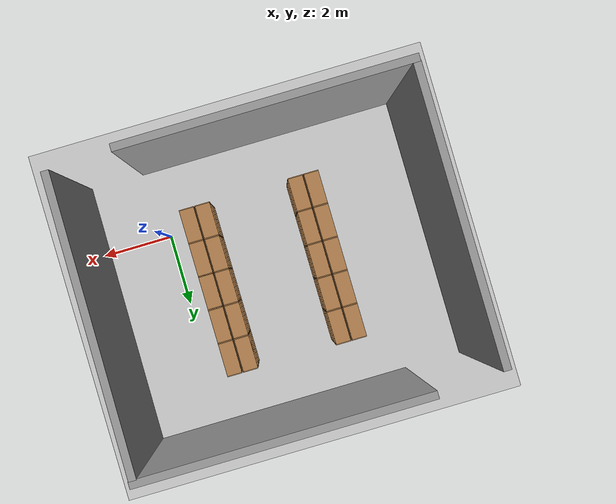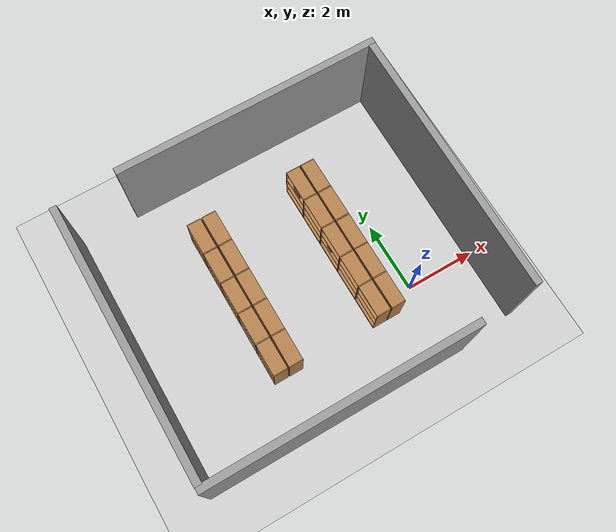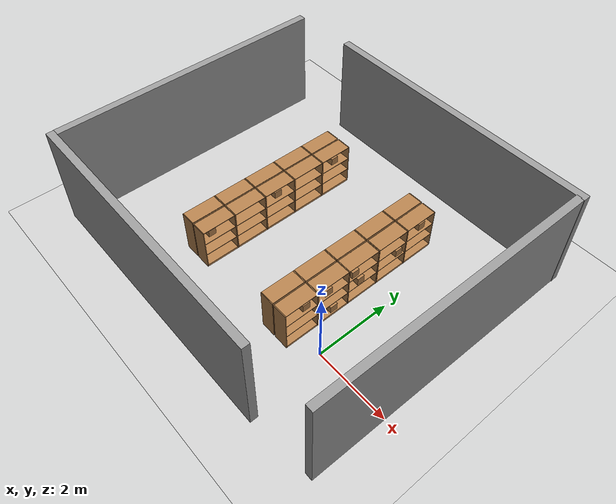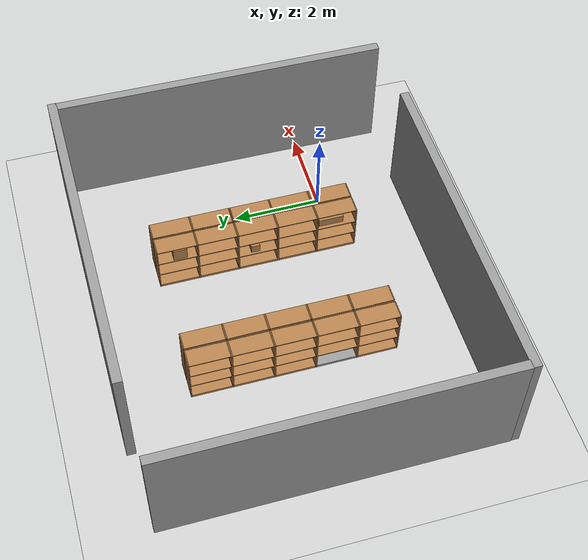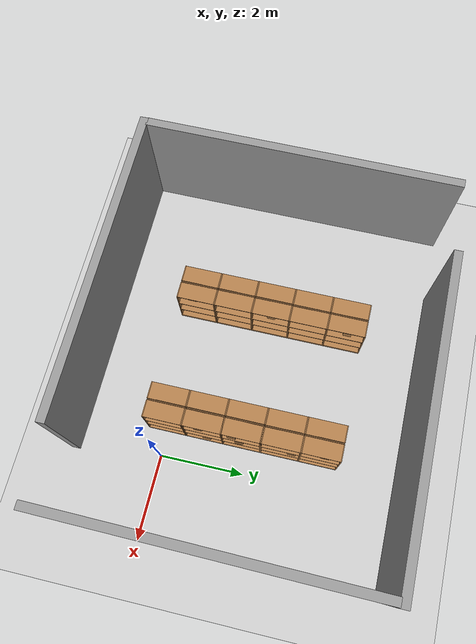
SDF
<sdf version="1.4">
 <world name="default">
  <light name="sun" type="directional">
   <pose>0 0 10 0 -0 0</pose>
   <diffuse>0.8 0.8 0.8 1</diffuse>
   <specular>0.2 0.2 0.2 1</specular>
   <attenuation>
    <range>1000</range>
    <constant>0.9</constant>
    <linear>0.01</linear>
    <quadratic>0.001</quadratic>
   </attenuation>
   <direction>-0.5 0.1 -0.9</direction>
  </light>
  <model name="ground_plane">
   <static>1</static>
   <link name="link">
    <collision name="collision">
     <geometry><plane><normal>0 0 1</normal><size>100 100</size></plane></geometry>
     <surface><friction><ode><mu>100</mu><mu2>50</mu2></ode></friction></surface>
    </collision>
    <visual name="visual">
     <cast_shadows>0</cast_shadows>
     <geometry><plane><normal>0 0 1</normal><size>100 100</size></plane></geometry>
     <material>
      <script><uri>file://media/materials/scripts/gazebo.material</uri><name>Gazebo/Grey</name></script>
     </material>
    </visual>
    <velocity_decay><linear>0</linear><angular>0</angular></velocity_decay>
   </link>
  </model>
  <physics type="ode">
   <max_step_size>0.001</max_step_size>
   <real_time_factor>1</real_time_factor>
   <real_time_update_rate>1000</real_time_update_rate>
   <gravity>0 0 -9.8</gravity>
  </physics>
  <scene><ambient>0.4 0.4 0.4 1</ambient><background>0.7 0.7 0.7 1</background><shadows>1</shadows></scene>
  <spherical_coordinates>
   <surface_model>EARTH_WGS84</surface_model>
   <latitude_deg>0</latitude_deg>
   <longitude_deg>0</longitude_deg>
   <elevation>0</elevation>
   <heading_deg>0</heading_deg>
  </spherical_coordinates>
  <model name="bookshelf">
   <static>0</static>
   <link name="link">
    <inertial><mass>1</mass></inertial>
    <collision name="back">
     <pose>0 0.005 0.6 0 -0 0</pose>
     <geometry><box><size>0.9 0.01 1.2</size></box></geometry>
    </collision>
    <visual name="visual1">
     <pose>0 0.005 0.6 0 -0 0</pose>
     <geometry><box><size>0.9 0.01 1.2</size></box></geometry>
     <material>
      <script><uri>file://media/materials/scripts/gazebo.material</uri><name>Gazebo/Wood</name></script>
     </material>
    </visual>
    <collision name="left_side">
     <pose>0.45 -0.195 0.6 0 -0 0</pose>
     <geometry><box><size>0.02 0.4 1.2</size></box></geometry>
    </collision>
    <visual name="visual2">
     <pose>0.45 -0.195 0.6 0 -0 0</pose>
     <geometry><box><size>0.02 0.4 1.2</size></box></geometry>
     <material>
      <script><uri>file://media/materials/scripts/gazebo.material</uri><name>Gazebo/Wood</name></script>
     </material>
    </visual>
    <collision name="right_side">
     <pose>-0.45 -0.195 0.6 0 -0 0</pose>
     <geometry><box><size>0.02 0.4 1.2</size></box></geometry>
    </collision>
    <visual name="visual3">
     <pose>-0.45 -0.195 0.6 0 -0 0</pose>
     <geometry><box><size>0.02 0.4 1.2</size></box></geometry>
     <material>
      <script><uri>file://media/materials/scripts/gazebo.material</uri><name>Gazebo/Wood</name></script>
     </material>
    </visual>
    <collision name="bottom">
     <pose>0 -0.195 0.03 0 -0 0</pose>
     <geometry><box><size>0.88 0.4 0.06</size></box></geometry>
    </collision>
    <visual name="visual4">
     <pose>0 -0.195 0.03 0 -0 0</pose>
     <geometry><box><size>0.88 0.4 0.06</size></box></geometry>
     <material>
      <script><uri>file://media/materials/scripts/gazebo.material</uri><name>Gazebo/Wood</name></script>
     </material>
    </visual>
    <collision name="top">
     <pose>0 -0.195 1.19 0 -0 0</pose>
     <geometry><box><size>0.88 0.4 0.02</size></box></geometry>
    </collision>
    <visual name="visual5">
     <pose>0 -0.195 1.19 0 -0 0</pose>
     <geometry><box><size>0.88 0.4 0.02</size></box></geometry>
     <material>
      <script><uri>file://media/materials/scripts/gazebo.material</uri><name>Gazebo/Wood</name></script>
     </material>
    </visual>
    <collision name="low_shelf">
     <pose>0 -0.195 0.43 0 -0 0</pose>
     <geometry><box><size>0.88 0.4 0.02</size></box></geometry>
    </collision>
    <visual name="visual6">
     <pose>0 -0.195 0.43 0 -0 0</pose>
     <geometry><box><size>0.88 0.4 0.02</size></box></geometry>
     <material>
      <script><uri>file://media/materials/scripts/gazebo.material</uri><name>Gazebo/Wood</name></script>
     </material>
    </visual>
    <collision name="high_shelf">
     <pose>0 -0.195 0.8 0 -0 0</pose>
     <geometry><box><size>0.88 0.4 0.02</size></box></geometry>
    </collision>
    <visual name="visual7">
     <pose>0 -0.195 0.8 0 -0 0</pose>
     <geometry><box><size>0.88 0.4 0.02</size></box></geometry>
     <material>
      <script><uri>file://media/materials/scripts/gazebo.material</uri><name>Gazebo/Wood</name></script>
     </material>
    </visual>
    <velocity_decay><linear>0</linear><angular>0</angular></velocity_decay>
   </link>
   <pose>-1 0 0 0 -0 1.5708</pose>
  </model>
  <model name="bookshelf_0">
   <static>1</static>
   <link name="link">
    <inertial><mass>1</mass></inertial>
    <collision name="back">
     <pose>0 0.005 0.6 0 -0 0</pose>
     <geometry><box><size>0.9 0.01 1.2</size></box></geometry>
    </collision>
    <visual name="visual1">
     <pose>0 0.005 0.6 0 -0 0</pose>
     <geometry><box><size>0.9 0.01 1.2</size></box></geometry>
     <material>
      <script><uri>file://media/materials/scripts/gazebo.material</uri><name>Gazebo/Wood</name></script>
     </material>
    </visual>
    <collision name="left_side">
     <pose>0.45 -0.195 0.6 0 -0 0</pose>
     <geometry><box><size>0.02 0.4 1.2</size></box></geometry>
    </collision>
    <visual name="visual2">
     <pose>0.45 -0.195 0.6 0 -0 0</pose>
     <geometry><box><size>0.02 0.4 1.2</size></box></geometry>
     <material>
      <script><uri>file://media/materials/scripts/gazebo.material</uri><name>Gazebo/Wood</name></script>
     </material>
    </visual>
    <collision name="right_side">
     <pose>-0.45 -0.195 0.6 0 -0 0</pose>
     <geometry><box><size>0.02 0.4 1.2</size></box></geometry>
    </collision>
    <visual name="visual3">
     <pose>-0.45 -0.195 0.6 0 -0 0</pose>
     <geometry><box><size>0.02 0.4 1.2</size></box></geometry>
     <material>
      <script><uri>file://media/materials/scripts/gazebo.material</uri><name>Gazebo/Wood</name></script>
     </material>
    </visual>
    <collision name="bottom">
     <pose>0 -0.195 0.03 0 -0 0</pose>
     <geometry><box><size>0.88 0.4 0.06</size></box></geometry>
    </collision>
    <visual name="visual4">
     <pose>0 -0.195 0.03 0 -0 0</pose>
     <geometry><box><size>0.88 0.4 0.06</size></box></geometry>
     <material>
      <script><uri>file://media/materials/scripts/gazebo.material</uri><name>Gazebo/Wood</name></script>
     </material>
    </visual>
    <collision name="top">
     <pose>0 -0.195 1.19 0 -0 0</pose>
     <geometry><box><size>0.88 0.4 0.02</size></box></geometry>
    </collision>
    <visual name="visual5">
     <pose>0 -0.195 1.19 0 -0 0</pose>
     <geometry><box><size>0.88 0.4 0.02</size></box></geometry>
     <material>
      <script><uri>file://media/materials/scripts/gazebo.material</uri><name>Gazebo/Wood</name></script>
     </material>
    </visual>
    <collision name="low_shelf">
     <pose>0 -0.195 0.43 0 -0 0</pose>
     <geometry><box><size>0.88 0.4 0.02</size></box></geometry>
    </collision>
    <visual name="visual6">
     <pose>0 -0.195 0.43 0 -0 0</pose>
     <geometry><box><size>0.88 0.4 0.02</size></box></geometry>
     <material>
      <script><uri>file://media/materials/scripts/gazebo.material</uri><name>Gazebo/Wood</name></script>
     </material>
    </visual>
    <collision name="high_shelf">
     <pose>0 -0.195 0.8 0 -0 0</pose>
     <geometry><box><size>0.88 0.4 0.02</size></box></geometry>
    </collision>
    <visual name="visual7">
     <pose>0 -0.195 0.8 0 -0 0</pose>
     <geometry><box><size>0.88 0.4 0.02</size></box></geometry>
     <material>
      <script><uri>file://media/materials/scripts/gazebo.material</uri><name>Gazebo/Wood</name></script>
     </material>
    </visual>
    <velocity_decay><linear>0</linear><angular>0</angular></velocity_decay>
   </link>
   <pose>-1 0.918842 0 0 -0 1.5708</pose>
  </model>
  <model name="bookshelf_1">
   <static>1</static>
   <link name="link">
    <inertial><mass>1</mass></inertial>
    <collision name="back">
     <pose>0 0.005 0.6 0 -0 0</pose>
     <geometry><box><size>0.9 0.01 1.2</size></box></geometry>
    </collision>
    <visual name="visual1">
     <pose>0 0.005 0.6 0 -0 0</pose>
     <geometry><box><size>0.9 0.01 1.2</size></box></geometry>
     <material>
      <script><uri>file://media/materials/scripts/gazebo.material</uri><name>Gazebo/Wood</name></script>
     </material>
    </visual>
    <collision name="left_side">
     <pose>0.45 -0.195 0.6 0 -0 0</pose>
     <geometry><box><size>0.02 0.4 1.2</size></box></geometry>
    </collision>
    <visual name="visual2">
     <pose>0.45 -0.195 0.6 0 -0 0</pose>
     <geometry><box><size>0.02 0.4 1.2</size></box></geometry>
     <material>
      <script><uri>file://media/materials/scripts/gazebo.material</uri><name>Gazebo/Wood</name></script>
     </material>
    </visual>
    <collision name="right_side">
     <pose>-0.45 -0.195 0.6 0 -0 0</pose>
     <geometry><box><size>0.02 0.4 1.2</size></box></geometry>
    </collision>
    <visual name="visual3">
     <pose>-0.45 -0.195 0.6 0 -0 0</pose>
     <geometry><box><size>0.02 0.4 1.2</size></box></geometry>
     <material>
      <script><uri>file://media/materials/scripts/gazebo.material</uri><name>Gazebo/Wood</name></script>
     </material>
    </visual>
    <collision name="bottom">
     <pose>0 -0.195 0.03 0 -0 0</pose>
     <geometry><box><size>0.88 0.4 0.06</size></box></geometry>
    </collision>
    <visual name="visual4">
     <pose>0 -0.195 0.03 0 -0 0</pose>
     <geometry><box><size>0.88 0.4 0.06</size></box></geometry>
     <material>
      <script><uri>file://media/materials/scripts/gazebo.material</uri><name>Gazebo/Wood</name></script>
     </material>
    </visual>
    <collision name="top">
     <pose>0 -0.195 1.19 0 -0 0</pose>
     <geometry><box><size>0.88 0.4 0.02</size></box></geometry>
    </collision>
    <visual name="visual5">
     <pose>0 -0.195 1.19 0 -0 0</pose>
     <geometry><box><size>0.88 0.4 0.02</size></box></geometry>
     <material>
      <script><uri>file://media/materials/scripts/gazebo.material</uri><name>Gazebo/Wood</name></script>
     </material>
    </visual>
    <collision name="low_shelf">
     <pose>0 -0.195 0.43 0 -0 0</pose>
     <geometry><box><size>0.88 0.4 0.02</size></box></geometry>
    </collision>
    <visual name="visual6">
     <pose>0 -0.195 0.43 0 -0 0</pose>
     <geometry><box><size>0.88 0.4 0.02</size></box></geometry>
     <material>
      <script><uri>file://media/materials/scripts/gazebo.material</uri><name>Gazebo/Wood</name></script>
     </material>
    </visual>
    <collision name="high_shelf">
     <pose>0 -0.195 0.8 0 -0 0</pose>
     <geometry><box><size>0.88 0.4 0.02</size></box></geometry>
    </collision>
    <visual name="visual7">
     <pose>0 -0.195 0.8 0 -0 0</pose>
     <geometry><box><size>0.88 0.4 0.02</size></box></geometry>
     <material>
      <script><uri>file://media/materials/scripts/gazebo.material</uri><name>Gazebo/Wood</name></script>
     </material>
    </visual>
    <velocity_decay><linear>0</linear><angular>0</angular></velocity_decay>
   </link>
   <pose>-1 1.83131 0 0 -0 1.5708</pose>
  </model>
  <model name="bookshelf_2">
   <static>1</static>
   <link name="link">
    <inertial><mass>1</mass></inertial>
    <collision name="back">
     <pose>0 0.005 0.6 0 -0 0</pose>
     <geometry><box><size>0.9 0.01 1.2</size></box></geometry>
    </collision>
    <visual name="visual1">
     <pose>0 0.005 0.6 0 -0 0</pose>
     <geometry><box><size>0.9 0.01 1.2</size></box></geometry>
     <material>
      <script><uri>file://media/materials/scripts/gazebo.material</uri><name>Gazebo/Wood</name></script>
     </material>
    </visual>
    <collision name="left_side">
     <pose>0.45 -0.195 0.6 0 -0 0</pose>
     <geometry><box><size>0.02 0.4 1.2</size></box></geometry>
    </collision>
    <visual name="visual2">
     <pose>0.45 -0.195 0.6 0 -0 0</pose>
     <geometry><box><size>0.02 0.4 1.2</size></box></geometry>
     <material>
      <script><uri>file://media/materials/scripts/gazebo.material</uri><name>Gazebo/Wood</name></script>
     </material>
    </visual>
    <collision name="right_side">
     <pose>-0.45 -0.195 0.6 0 -0 0</pose>
     <geometry><box><size>0.02 0.4 1.2</size></box></geometry>
    </collision>
    <visual name="visual3">
     <pose>-0.45 -0.195 0.6 0 -0 0</pose>
     <geometry><box><size>0.02 0.4 1.2</size></box></geometry>
     <material>
      <script><uri>file://media/materials/scripts/gazebo.material</uri><name>Gazebo/Wood</name></script>
     </material>
    </visual>
    <collision name="bottom">
     <pose>0 -0.195 0.03 0 -0 0</pose>
     <geometry><box><size>0.88 0.4 0.06</size></box></geometry>
    </collision>
    <visual name="visual4">
     <pose>0 -0.195 0.03 0 -0 0</pose>
     <geometry><box><size>0.88 0.4 0.06</size></box></geometry>
     <material>
      <script><uri>file://media/materials/scripts/gazebo.material</uri><name>Gazebo/Wood</name></script>
     </material>
    </visual>
    <collision name="top">
     <pose>0 -0.195 1.19 0 -0 0</pose>
     <geometry><box><size>0.88 0.4 0.02</size></box></geometry>
    </collision>
    <visual name="visual5">
     <pose>0 -0.195 1.19 0 -0 0</pose>
     <geometry><box><size>0.88 0.4 0.02</size></box></geometry>
     <material>
      <script><uri>file://media/materials/scripts/gazebo.material</uri><name>Gazebo/Wood</name></script>
     </material>
    </visual>
    <collision name="low_shelf">
     <pose>0 -0.195 0.43 0 -0 0</pose>
     <geometry><box><size>0.88 0.4 0.02</size></box></geometry>
    </collision>
    <visual name="visual6">
     <pose>0 -0.195 0.43 0 -0 0</pose>
     <geometry><box><size>0.88 0.4 0.02</size></box></geometry>
     <material>
      <script><uri>file://media/materials/scripts/gazebo.material</uri><name>Gazebo/Wood</name></script>
     </material>
    </visual>
    <collision name="high_shelf">
     <pose>0 -0.195 0.8 0 -0 0</pose>
     <geometry><box><size>0.88 0.4 0.02</size></box></geometry>
    </collision>
    <visual name="visual7">
     <pose>0 -0.195 0.8 0 -0 0</pose>
     <geometry><box><size>0.88 0.4 0.02</size></box></geometry>
     <material>
      <script><uri>file://media/materials/scripts/gazebo.material</uri><name>Gazebo/Wood</name></script>
     </material>
    </visual>
    <velocity_decay><linear>0</linear><angular>0</angular></velocity_decay>
   </link>
   <pose>-4 1.8376 0 0 -0 1.5708</pose>
  </model>
  <model name="bookshelf_3">
   <static>1</static>
   <link name="link">
    <inertial><mass>1</mass></inertial>
    <collision name="back">
     <pose>0 0.005 0.6 0 -0 0</pose>
     <geometry><box><size>0.9 0.01 1.2</size></box></geometry>
    </collision>
    <visual name="visual1">
     <pose>0 0.005 0.6 0 -0 0</pose>
     <geometry><box><size>0.9 0.01 1.2</size></box></geometry>
     <material>
      <script><uri>file://media/materials/scripts/gazebo.material</uri><name>Gazebo/Wood</name></script>
     </material>
    </visual>
    <collision name="left_side">
     <pose>0.45 -0.195 0.6 0 -0 0</pose>
     <geometry><box><size>0.02 0.4 1.2</size></box></geometry>
    </collision>
    <visual name="visual2">
     <pose>0.45 -0.195 0.6 0 -0 0</pose>
     <geometry><box><size>0.02 0.4 1.2</size></box></geometry>
     <material>
      <script><uri>file://media/materials/scripts/gazebo.material</uri><name>Gazebo/Wood</name></script>
     </material>
    </visual>
    <collision name="right_side">
     <pose>-0.45 -0.195 0.6 0 -0 0</pose>
     <geometry><box><size>0.02 0.4 1.2</size></box></geometry>
    </collision>
    <visual name="visual3">
     <pose>-0.45 -0.195 0.6 0 -0 0</pose>
     <geometry><box><size>0.02 0.4 1.2</size></box></geometry>
     <material>
      <script><uri>file://media/materials/scripts/gazebo.material</uri><name>Gazebo/Wood</name></script>
     </material>
    </visual>
    <collision name="bottom">
     <pose>0 -0.195 0.03 0 -0 0</pose>
     <geometry><box><size>0.88 0.4 0.06</size></box></geometry>
    </collision>
    <visual name="visual4">
     <pose>0 -0.195 0.03 0 -0 0</pose>
     <geometry><box><size>0.88 0.4 0.06</size></box></geometry>
     <material>
      <script><uri>file://media/materials/scripts/gazebo.material</uri><name>Gazebo/Wood</name></script>
     </material>
    </visual>
    <collision name="top">
     <pose>0 -0.195 1.19 0 -0 0</pose>
     <geometry><box><size>0.88 0.4 0.02</size></box></geometry>
    </collision>
    <visual name="visual5">
     <pose>0 -0.195 1.19 0 -0 0</pose>
     <geometry><box><size>0.88 0.4 0.02</size></box></geometry>
     <material>
      <script><uri>file://media/materials/scripts/gazebo.material</uri><name>Gazebo/Wood</name></script>
     </material>
    </visual>
    <collision name="low_shelf">
     <pose>0 -0.195 0.43 0 -0 0</pose>
     <geometry><box><size>0.88 0.4 0.02</size></box></geometry>
    </collision>
    <visual name="visual6">
     <pose>0 -0.195 0.43 0 -0 0</pose>
     <geometry><box><size>0.88 0.4 0.02</size></box></geometry>
     <material>
      <script><uri>file://media/materials/scripts/gazebo.material</uri><name>Gazebo/Wood</name></script>
     </material>
    </visual>
    <collision name="high_shelf">
     <pose>0 -0.195 0.8 0 -0 0</pose>
     <geometry><box><size>0.88 0.4 0.02</size></box></geometry>
    </collision>
    <visual name="visual7">
     <pose>0 -0.195 0.8 0 -0 0</pose>
     <geometry><box><size>0.88 0.4 0.02</size></box></geometry>
     <material>
      <script><uri>file://media/materials/scripts/gazebo.material</uri><name>Gazebo/Wood</name></script>
     </material>
    </visual>
    <velocity_decay><linear>0</linear><angular>0</angular></velocity_decay>
   </link>
   <pose>-4 2.7564 0 0 -0 1.5708</pose>
  </model>
  <model name="bookshelf_4">
   <static>1</static>
   <link name="link">
    <inertial><mass>1</mass></inertial>
    <collision name="back">
     <pose>0 0.005 0.6 0 -0 0</pose>
     <geometry><box><size>0.9 0.01 1.2</size></box></geometry>
    </collision>
    <visual name="visual1">
     <pose>0 0.005 0.6 0 -0 0</pose>
     <geometry><box><size>0.9 0.01 1.2</size></box></geometry>
     <material>
      <script><uri>file://media/materials/scripts/gazebo.material</uri><name>Gazebo/Wood</name></script>
     </material>
    </visual>
    <collision name="left_side">
     <pose>0.45 -0.195 0.6 0 -0 0</pose>
     <geometry><box><size>0.02 0.4 1.2</size></box></geometry>
    </collision>
    <visual name="visual2">
     <pose>0.45 -0.195 0.6 0 -0 0</pose>
     <geometry><box><size>0.02 0.4 1.2</size></box></geometry>
     <material>
      <script><uri>file://media/materials/scripts/gazebo.material</uri><name>Gazebo/Wood</name></script>
     </material>
    </visual>
    <collision name="right_side">
     <pose>-0.45 -0.195 0.6 0 -0 0</pose>
     <geometry><box><size>0.02 0.4 1.2</size></box></geometry>
    </collision>
    <visual name="visual3">
     <pose>-0.45 -0.195 0.6 0 -0 0</pose>
     <geometry><box><size>0.02 0.4 1.2</size></box></geometry>
     <material>
      <script><uri>file://media/materials/scripts/gazebo.material</uri><name>Gazebo/Wood</name></script>
     </material>
    </visual>
    <collision name="bottom">
     <pose>0 -0.195 0.03 0 -0 0</pose>
     <geometry><box><size>0.88 0.4 0.06</size></box></geometry>
    </collision>
    <visual name="visual4">
     <pose>0 -0.195 0.03 0 -0 0</pose>
     <geometry><box><size>0.88 0.4 0.06</size></box></geometry>
     <material>
      <script><uri>file://media/materials/scripts/gazebo.material</uri><name>Gazebo/Wood</name></script>
     </material>
    </visual>
    <collision name="top">
     <pose>0 -0.195 1.19 0 -0 0</pose>
     <geometry><box><size>0.88 0.4 0.02</size></box></geometry>
    </collision>
    <visual name="visual5">
     <pose>0 -0.195 1.19 0 -0 0</pose>
     <geometry><box><size>0.88 0.4 0.02</size></box></geometry>
     <material>
      <script><uri>file://media/materials/scripts/gazebo.material</uri><name>Gazebo/Wood</name></script>
     </material>
    </visual>
    <collision name="low_shelf">
     <pose>0 -0.195 0.43 0 -0 0</pose>
     <geometry><box><size>0.88 0.4 0.02</size></box></geometry>
    </collision>
    <visual name="visual6">
     <pose>0 -0.195 0.43 0 -0 0</pose>
     <geometry><box><size>0.88 0.4 0.02</size></box></geometry>
     <material>
      <script><uri>file://media/materials/scripts/gazebo.material</uri><name>Gazebo/Wood</name></script>
     </material>
    </visual>
    <collision name="high_shelf">
     <pose>0 -0.195 0.8 0 -0 0</pose>
     <geometry><box><size>0.88 0.4 0.02</size></box></geometry>
    </collision>
    <visual name="visual7">
     <pose>0 -0.195 0.8 0 -0 0</pose>
     <geometry><box><size>0.88 0.4 0.02</size></box></geometry>
     <material>
      <script><uri>file://media/materials/scripts/gazebo.material</uri><name>Gazebo/Wood</name></script>
     </material>
    </visual>
    <velocity_decay><linear>0</linear><angular>0</angular></velocity_decay>
   </link>
   <pose>-4 3.6752 0 0 -0 1.5708</pose>
  </model>
  <model name="bookshelf_5">
   <static>1</static>
   <link name="link">
    <inertial><mass>1</mass></inertial>
    <collision name="back">
     <pose>0 0.005 0.6 0 -0 0</pose>
     <geometry><box><size>0.9 0.01 1.2</size></box></geometry>
    </collision>
    <visual name="visual1">
     <pose>0 0.005 0.6 0 -0 0</pose>
     <geometry><box><size>0.9 0.01 1.2</size></box></geometry>
     <material>
      <script><uri>file://media/materials/scripts/gazebo.material</uri><name>Gazebo/Wood</name></script>
     </material>
    </visual>
    <collision name="left_side">
     <pose>0.45 -0.195 0.6 0 -0 0</pose>
     <geometry><box><size>0.02 0.4 1.2</size></box></geometry>
    </collision>
    <visual name="visual2">
     <pose>0.45 -0.195 0.6 0 -0 0</pose>
     <geometry><box><size>0.02 0.4 1.2</size></box></geometry>
     <material>
      <script><uri>file://media/materials/scripts/gazebo.material</uri><name>Gazebo/Wood</name></script>
     </material>
    </visual>
    <collision name="right_side">
     <pose>-0.45 -0.195 0.6 0 -0 0</pose>
     <geometry><box><size>0.02 0.4 1.2</size></box></geometry>
    </collision>
    <visual name="visual3">
     <pose>-0.45 -0.195 0.6 0 -0 0</pose>
     <geometry><box><size>0.02 0.4 1.2</size></box></geometry>
     <material>
      <script><uri>file://media/materials/scripts/gazebo.material</uri><name>Gazebo/Wood</name></script>
     </material>
    </visual>
    <collision name="bottom">
     <pose>0 -0.195 0.03 0 -0 0</pose>
     <geometry><box><size>0.88 0.4 0.06</size></box></geometry>
    </collision>
    <visual name="visual4">
     <pose>0 -0.195 0.03 0 -0 0</pose>
     <geometry><box><size>0.88 0.4 0.06</size></box></geometry>
     <material>
      <script><uri>file://media/materials/scripts/gazebo.material</uri><name>Gazebo/Wood</name></script>
     </material>
    </visual>
    <collision name="top">
     <pose>0 -0.195 1.19 0 -0 0</pose>
     <geometry><box><size>0.88 0.4 0.02</size></box></geometry>
    </collision>
    <visual name="visual5">
     <pose>0 -0.195 1.19 0 -0 0</pose>
     <geometry><box><size>0.88 0.4 0.02</size></box></geometry>
     <material>
      <script><uri>file://media/materials/scripts/gazebo.material</uri><name>Gazebo/Wood</name></script>
     </material>
    </visual>
    <collision name="low_shelf">
     <pose>0 -0.195 0.43 0 -0 0</pose>
     <geometry><box><size>0.88 0.4 0.02</size></box></geometry>
    </collision>
    <visual name="visual6">
     <pose>0 -0.195 0.43 0 -0 0</pose>
     <geometry><box><size>0.88 0.4 0.02</size></box></geometry>
     <material>
      <script><uri>file://media/materials/scripts/gazebo.material</uri><name>Gazebo/Wood</name></script>
     </material>
    </visual>
    <collision name="high_shelf">
     <pose>0 -0.195 0.8 0 -0 0</pose>
     <geometry><box><size>0.88 0.4 0.02</size></box></geometry>
    </collision>
    <visual name="visual7">
     <pose>0 -0.195 0.8 0 -0 0</pose>
     <geometry><box><size>0.88 0.4 0.02</size></box></geometry>
     <material>
      <script><uri>file://media/materials/scripts/gazebo.material</uri><name>Gazebo/Wood</name></script>
     </material>
    </visual>
    <velocity_decay><linear>0</linear><angular>0</angular></velocity_decay>
   </link>
   <pose>-4.05 0 0 0 0 -1.5708</pose>
  </model>
  <model name="bookshelf_6">
   <static>1</static>
   <link name="link">
    <inertial><mass>1</mass></inertial>
    <collision name="back">
     <pose>0 0.005 0.6 0 -0 0</pose>
     <geometry><box><size>0.9 0.01 1.2</size></box></geometry>
    </collision>
    <visual name="visual1">
     <pose>0 0.005 0.6 0 -0 0</pose>
     <geometry><box><size>0.9 0.01 1.2</size></box></geometry>
     <material>
      <script><uri>file://media/materials/scripts/gazebo.material</uri><name>Gazebo/Wood</name></script>
     </material>
    </visual>
    <collision name="left_side">
     <pose>0.45 -0.195 0.6 0 -0 0</pose>
     <geometry><box><size>0.02 0.4 1.2</size></box></geometry>
    </collision>
    <visual name="visual2">
     <pose>0.45 -0.195 0.6 0 -0 0</pose>
     <geometry><box><size>0.02 0.4 1.2</size></box></geometry>
     <material>
      <script><uri>file://media/materials/scripts/gazebo.material</uri><name>Gazebo/Wood</name></script>
     </material>
    </visual>
    <collision name="right_side">
     <pose>-0.45 -0.195 0.6 0 -0 0</pose>
     <geometry><box><size>0.02 0.4 1.2</size></box></geometry>
    </collision>
    <visual name="visual3">
     <pose>-0.45 -0.195 0.6 0 -0 0</pose>
     <geometry><box><size>0.02 0.4 1.2</size></box></geometry>
     <material>
      <script><uri>file://media/materials/scripts/gazebo.material</uri><name>Gazebo/Wood</name></script>
     </material>
    </visual>
    <collision name="bottom">
     <pose>0 -0.195 0.03 0 -0 0</pose>
     <geometry><box><size>0.88 0.4 0.06</size></box></geometry>
    </collision>
    <visual name="visual4">
     <pose>0 -0.195 0.03 0 -0 0</pose>
     <geometry><box><size>0.88 0.4 0.06</size></box></geometry>
     <material>
      <script><uri>file://media/materials/scripts/gazebo.material</uri><name>Gazebo/Grey</name></script>
     </material>
    </visual>
    <collision name="top">
     <pose>0 -0.195 1.19 0 -0 0</pose>
     <geometry><box><size>0.88 0.4 0.02</size></box></geometry>
    </collision>
    <visual name="visual5">
     <pose>0 -0.195 1.19 0 -0 0</pose>
     <geometry><box><size>0.88 0.4 0.02</size></box></geometry>
     <material>
      <script><uri>file://media/materials/scripts/gazebo.material</uri><name>Gazebo/Wood</name></script>
     </material>
    </visual>
    <collision name="low_shelf">
     <pose>0 -0.195 0.43 0 -0 0</pose>
     <geometry><box><size>0.88 0.4 0.02</size></box></geometry>
    </collision>
    <visual name="visual6">
     <pose>0 -0.195 0.43 0 -0 0</pose>
     <geometry><box><size>0.88 0.4 0.02</size></box></geometry>
     <material>
      <script><uri>file://media/materials/scripts/gazebo.material</uri><name>Gazebo/Wood</name></script>
     </material>
    </visual>
    <collision name="high_shelf">
     <pose>0 -0.195 0.8 0 -0 0</pose>
     <geometry><box><size>0.88 0.4 0.02</size></box></geometry>
    </collision>
    <visual name="visual7">
     <pose>0 -0.195 0.8 0 -0 0</pose>
     <geometry><box><size>0.88 0.4 0.02</size></box></geometry>
     <material>
      <script><uri>file://media/materials/scripts/gazebo.material</uri><name>Gazebo/Wood</name></script>
     </material>
    </visual>
    <velocity_decay><linear>0</linear><angular>0</angular></velocity_decay>
   </link>
   <pose>-4.05 0.9188 0 0 0 -1.5708</pose>
  </model>
  <model name="bookshelf_7">
   <static>1</static>
   <link name="link">
    <inertial><mass>1</mass></inertial>
    <collision name="back">
     <pose>0 0.005 0.6 0 -0 0</pose>
     <geometry><box><size>0.9 0.01 1.2</size></box></geometry>
    </collision>
    <visual name="visual1">
     <pose>0 0.005 0.6 0 -0 0</pose>
     <geometry><box><size>0.9 0.01 1.2</size></box></geometry>
     <material>
      <script><uri>file://media/materials/scripts/gazebo.material</uri><name>Gazebo/Wood</name></script>
     </material>
    </visual>
    <collision name="left_side">
     <pose>0.45 -0.195 0.6 0 -0 0</pose>
     <geometry><box><size>0.02 0.4 1.2</size></box></geometry>
    </collision>
    <visual name="visual2">
     <pose>0.45 -0.195 0.6 0 -0 0</pose>
     <geometry><box><size>0.02 0.4 1.2</size></box></geometry>
     <material>
      <script><uri>file://media/materials/scripts/gazebo.material</uri><name>Gazebo/Wood</name></script>
     </material>
    </visual>
    <collision name="right_side">
     <pose>-0.45 -0.195 0.6 0 -0 0</pose>
     <geometry><box><size>0.02 0.4 1.2</size></box></geometry>
    </collision>
    <visual name="visual3">
     <pose>-0.45 -0.195 0.6 0 -0 0</pose>
     <geometry><box><size>0.02 0.4 1.2</size></box></geometry>
     <material>
      <script><uri>file://media/materials/scripts/gazebo.material</uri><name>Gazebo/Wood</name></script>
     </material>
    </visual>
    <collision name="bottom">
     <pose>0 -0.195 0.03 0 -0 0</pose>
     <geometry><box><size>0.88 0.4 0.06</size></box></geometry>
    </collision>
    <visual name="visual4">
     <pose>0 -0.195 0.03 0 -0 0</pose>
     <geometry><box><size>0.88 0.4 0.06</size></box></geometry>
     <material>
      <script><uri>file://media/materials/scripts/gazebo.material</uri><name>Gazebo/Wood</name></script>
     </material>
    </visual>
    <collision name="top">
     <pose>0 -0.195 1.19 0 -0 0</pose>
     <geometry><box><size>0.88 0.4 0.02</size></box></geometry>
    </collision>
    <visual name="visual5">
     <pose>0 -0.195 1.19 0 -0 0</pose>
     <geometry><box><size>0.88 0.4 0.02</size></box></geometry>
     <material>
      <script><uri>file://media/materials/scripts/gazebo.material</uri><name>Gazebo/Wood</name></script>
     </material>
    </visual>
    <collision name="low_shelf">
     <pose>0 -0.195 0.43 0 -0 0</pose>
     <geometry><box><size>0.88 0.4 0.02</size></box></geometry>
    </collision>
    <visual name="visual6">
     <pose>0 -0.195 0.43 0 -0 0</pose>
     <geometry><box><size>0.88 0.4 0.02</size></box></geometry>
     <material>
      <script><uri>file://media/materials/scripts/gazebo.material</uri><name>Gazebo/Wood</name></script>
     </material>
    </visual>
    <collision name="high_shelf">
     <pose>0 -0.195 0.8 0 -0 0</pose>
     <geometry><box><size>0.88 0.4 0.02</size></box></geometry>
    </collision>
    <visual name="visual7">
     <pose>0 -0.195 0.8 0 -0 0</pose>
     <geometry><box><size>0.88 0.4 0.02</size></box></geometry>
     <material>
      <script><uri>file://media/materials/scripts/gazebo.material</uri><name>Gazebo/Wood</name></script>
     </material>
    </visual>
    <velocity_decay><linear>0</linear><angular>0</angular></velocity_decay>
   </link>
   <pose>-4.05 1.8376 0 0 0 -1.5708</pose>
  </model>
  <model name="bookshelf_8">
   <static>1</static>
   <link name="link">
    <inertial><mass>1</mass></inertial>
    <collision name="back">
     <pose>0 0.005 0.6 0 -0 0</pose>
     <geometry><box><size>0.9 0.01 1.2</size></box></geometry>
    </collision>
    <visual name="visual1">
     <pose>0 0.005 0.6 0 -0 0</pose>
     <geometry><box><size>0.9 0.01 1.2</size></box></geometry>
     <material>
      <script><uri>file://media/materials/scripts/gazebo.material</uri><name>Gazebo/Wood</name></script>
     </material>
    </visual>
    <collision name="left_side">
     <pose>0.45 -0.195 0.6 0 -0 0</pose>
     <geometry><box><size>0.02 0.4 1.2</size></box></geometry>
    </collision>
    <visual name="visual2">
     <pose>0.45 -0.195 0.6 0 -0 0</pose>
     <geometry><box><size>0.02 0.4 1.2</size></box></geometry>
     <material>
      <script><uri>file://media/materials/scripts/gazebo.material</uri><name>Gazebo/Wood</name></script>
     </material>
    </visual>
    <collision name="right_side">
     <pose>-0.45 -0.195 0.6 0 -0 0</pose>
     <geometry><box><size>0.02 0.4 1.2</size></box></geometry>
    </collision>
    <visual name="visual3">
     <pose>-0.45 -0.195 0.6 0 -0 0</pose>
     <geometry><box><size>0.02 0.4 1.2</size></box></geometry>
     <material>
      <script><uri>file://media/materials/scripts/gazebo.material</uri><name>Gazebo/Wood</name></script>
     </material>
    </visual>
    <collision name="bottom">
     <pose>0 -0.195 0.03 0 -0 0</pose>
     <geometry><box><size>0.88 0.4 0.06</size></box></geometry>
    </collision>
    <visual name="visual4">
     <pose>0 -0.195 0.03 0 -0 0</pose>
     <geometry><box><size>0.88 0.4 0.06</size></box></geometry>
     <material>
      <script><uri>file://media/materials/scripts/gazebo.material</uri><name>Gazebo/Wood</name></script>
     </material>
    </visual>
    <collision name="top">
     <pose>0 -0.195 1.19 0 -0 0</pose>
     <geometry><box><size>0.88 0.4 0.02</size></box></geometry>
    </collision>
    <visual name="visual5">
     <pose>0 -0.195 1.19 0 -0 0</pose>
     <geometry><box><size>0.88 0.4 0.02</size></box></geometry>
     <material>
      <script><uri>file://media/materials/scripts/gazebo.material</uri><name>Gazebo/Wood</name></script>
     </material>
    </visual>
    <collision name="low_shelf">
     <pose>0 -0.195 0.43 0 -0 0</pose>
     <geometry><box><size>0.88 0.4 0.02</size></box></geometry>
    </collision>
    <visual name="visual6">
     <pose>0 -0.195 0.43 0 -0 0</pose>
     <geometry><box><size>0.88 0.4 0.02</size></box></geometry>
     <material>
      <script><uri>file://media/materials/scripts/gazebo.material</uri><name>Gazebo/Wood</name></script>
     </material>
    </visual>
    <collision name="high_shelf">
     <pose>0 -0.195 0.8 0 -0 0</pose>
     <geometry><box><size>0.88 0.4 0.02</size></box></geometry>
    </collision>
    <visual name="visual7">
     <pose>0 -0.195 0.8 0 -0 0</pose>
     <geometry><box><size>0.88 0.4 0.02</size></box></geometry>
     <material>
      <script><uri>file://media/materials/scripts/gazebo.material</uri><name>Gazebo/Wood</name></script>
     </material>
    </visual>
    <velocity_decay><linear>0</linear><angular>0</angular></velocity_decay>
   </link>
   <pose>-4.05 2.7564 0 0 0 -1.5708</pose>
  </model>
  <model name="bookshelf_9">
   <static>1</static>
   <link name="link">
    <inertial><mass>1</mass></inertial>
    <collision name="back">
     <pose>0 0.005 0.6 0 -0 0</pose>
     <geometry><box><size>0.9 0.01 1.2</size></box></geometry>
    </collision>
    <visual name="visual1">
     <pose>0 0.005 0.6 0 -0 0</pose>
     <geometry><box><size>0.9 0.01 1.2</size></box></geometry>
     <material>
      <script><uri>file://media/materials/scripts/gazebo.material</uri><name>Gazebo/Wood</name></script>
     </material>
    </visual>
    <collision name="left_side">
     <pose>0.45 -0.195 0.6 0 -0 0</pose>
     <geometry><box><size>0.02 0.4 1.2</size></box></geometry>
    </collision>
    <visual name="visual2">
     <pose>0.45 -0.195 0.6 0 -0 0</pose>
     <geometry><box><size>0.02 0.4 1.2</size></box></geometry>
     <material>
      <script><uri>file://media/materials/scripts/gazebo.material</uri><name>Gazebo/Wood</name></script>
     </material>
    </visual>
    <collision name="right_side">
     <pose>-0.45 -0.195 0.6 0 -0 0</pose>
     <geometry><box><size>0.02 0.4 1.2</size></box></geometry>
    </collision>
    <visual name="visual3">
     <pose>-0.45 -0.195 0.6 0 -0 0</pose>
     <geometry><box><size>0.02 0.4 1.2</size></box></geometry>
     <material>
      <script><uri>file://media/materials/scripts/gazebo.material</uri><name>Gazebo/Wood</name></script>
     </material>
    </visual>
    <collision name="bottom">
     <pose>0 -0.195 0.03 0 -0 0</pose>
     <geometry><box><size>0.88 0.4 0.06</size></box></geometry>
    </collision>
    <visual name="visual4">
     <pose>0 -0.195 0.03 0 -0 0</pose>
     <geometry><box><size>0.88 0.4 0.06</size></box></geometry>
     <material>
      <script><uri>file://media/materials/scripts/gazebo.material</uri><name>Gazebo/Wood</name></script>
     </material>
    </visual>
    <collision name="top">
     <pose>0 -0.195 1.19 0 -0 0</pose>
     <geometry><box><size>0.88 0.4 0.02</size></box></geometry>
    </collision>
    <visual name="visual5">
     <pose>0 -0.195 1.19 0 -0 0</pose>
     <geometry><box><size>0.88 0.4 0.02</size></box></geometry>
     <material>
      <script><uri>file://media/materials/scripts/gazebo.material</uri><name>Gazebo/Wood</name></script>
     </material>
    </visual>
    <collision name="low_shelf">
     <pose>0 -0.195 0.43 0 -0 0</pose>
     <geometry><box><size>0.88 0.4 0.02</size></box></geometry>
    </collision>
    <visual name="visual6">
     <pose>0 -0.195 0.43 0 -0 0</pose>
     <geometry><box><size>0.88 0.4 0.02</size></box></geometry>
     <material>
      <script><uri>file://media/materials/scripts/gazebo.material</uri><name>Gazebo/Wood</name></script>
     </material>
    </visual>
    <collision name="high_shelf">
     <pose>0 -0.195 0.8 0 -0 0</pose>
     <geometry><box><size>0.88 0.4 0.02</size></box></geometry>
    </collision>
    <visual name="visual7">
     <pose>0 -0.195 0.8 0 -0 0</pose>
     <geometry><box><size>0.88 0.4 0.02</size></box></geometry>
     <material>
      <script><uri>file://media/materials/scripts/gazebo.material</uri><name>Gazebo/Wood</name></script>
     </material>
    </visual>
    <velocity_decay><linear>0</linear><angular>0</angular></velocity_decay>
   </link>
   <pose>-4.05 3.6752 0 0 0 -1.5708</pose>
  </model>
  <model name="bookshelf_10">
   <static>1</static>
   <link name="link">
    <inertial><mass>1</mass></inertial>
    <collision name="back">
     <pose>0 0.005 0.6 0 -0 0</pose>
     <geometry><box><size>0.9 0.01 1.2</size></box></geometry>
    </collision>
    <visual name="visual1">
     <pose>0 0.005 0.6 0 -0 0</pose>
     <geometry><box><size>0.9 0.01 1.2</size></box></geometry>
     <material>
      <script><uri>file://media/materials/scripts/gazebo.material</uri><name>Gazebo/Wood</name></script>
     </material>
    </visual>
    <collision name="left_side">
     <pose>0.45 -0.195 0.6 0 -0 0</pose>
     <geometry><box><size>0.02 0.4 1.2</size></box></geometry>
    </collision>
    <visual name="visual2">
     <pose>0.45 -0.195 0.6 0 -0 0</pose>
     <geometry><box><size>0.02 0.4 1.2</size></box></geometry>
     <material>
      <script><uri>file://media/materials/scripts/gazebo.material</uri><name>Gazebo/Wood</name></script>
     </material>
    </visual>
    <collision name="right_side">
     <pose>-0.45 -0.195 0.6 0 -0 0</pose>
     <geometry><box><size>0.02 0.4 1.2</size></box></geometry>
    </collision>
    <visual name="visual3">
     <pose>-0.45 -0.195 0.6 0 -0 0</pose>
     <geometry><box><size>0.02 0.4 1.2</size></box></geometry>
     <material>
      <script><uri>file://media/materials/scripts/gazebo.material</uri><name>Gazebo/Wood</name></script>
     </material>
    </visual>
    <collision name="bottom">
     <pose>0 -0.195 0.03 0 -0 0</pose>
     <geometry><box><size>0.88 0.4 0.06</size></box></geometry>
    </collision>
    <visual name="visual4">
     <pose>0 -0.195 0.03 0 -0 0</pose>
     <geometry><box><size>0.88 0.4 0.06</size></box></geometry>
     <material>
      <script><uri>file://media/materials/scripts/gazebo.material</uri><name>Gazebo/Wood</name></script>
     </material>
    </visual>
    <collision name="top">
     <pose>0 -0.195 1.19 0 -0 0</pose>
     <geometry><box><size>0.88 0.4 0.02</size></box></geometry>
    </collision>
    <visual name="visual5">
     <pose>0 -0.195 1.19 0 -0 0</pose>
     <geometry><box><size>0.88 0.4 0.02</size></box></geometry>
     <material>
      <script><uri>file://media/materials/scripts/gazebo.material</uri><name>Gazebo/Wood</name></script>
     </material>
    </visual>
    <collision name="low_shelf">
     <pose>0 -0.195 0.43 0 -0 0</pose>
     <geometry><box><size>0.88 0.4 0.02</size></box></geometry>
    </collision>
    <visual name="visual6">
     <pose>0 -0.195 0.43 0 -0 0</pose>
     <geometry><box><size>0.88 0.4 0.02</size></box></geometry>
     <material>
      <script><uri>file://media/materials/scripts/gazebo.material</uri><name>Gazebo/Wood</name></script>
     </material>
    </visual>
    <collision name="high_shelf">
     <pose>0 -0.195 0.8 0 -0 0</pose>
     <geometry><box><size>0.88 0.4 0.02</size></box></geometry>
    </collision>
    <visual name="visual7">
     <pose>0 -0.195 0.8 0 -0 0</pose>
     <geometry><box><size>0.88 0.4 0.02</size></box></geometry>
     <material>
      <script><uri>file://media/materials/scripts/gazebo.material</uri><name>Gazebo/Wood</name></script>
     </material>
    </visual>
    <velocity_decay><linear>0</linear><angular>0</angular></velocity_decay>
   </link>
   <pose>-1 2.7564 0 0 -0 1.5708</pose>
  </model>
  <model name="bookshelf_11">
   <static>1</static>
   <link name="link">
    <inertial><mass>1</mass></inertial>
    <collision name="back">
     <pose>0 0.005 0.6 0 -0 0</pose>
     <geometry><box><size>0.9 0.01 1.2</size></box></geometry>
    </collision>
    <visual name="visual1">
     <pose>0 0.005 0.6 0 -0 0</pose>
     <geometry><box><size>0.9 0.01 1.2</size></box></geometry>
     <material>
      <script><uri>file://media/materials/scripts/gazebo.material</uri><name>Gazebo/Wood</name></script>
     </material>
    </visual>
    <collision name="left_side">
     <pose>0.45 -0.195 0.6 0 -0 0</pose>
     <geometry><box><size>0.02 0.4 1.2</size></box></geometry>
    </collision>
    <visual name="visual2">
     <pose>0.45 -0.195 0.6 0 -0 0</pose>
     <geometry><box><size>0.02 0.4 1.2</size></box></geometry>
     <material>
      <script><uri>file://media/materials/scripts/gazebo.material</uri><name>Gazebo/Wood</name></script>
     </material>
    </visual>
    <collision name="right_side">
     <pose>-0.45 -0.195 0.6 0 -0 0</pose>
     <geometry><box><size>0.02 0.4 1.2</size></box></geometry>
    </collision>
    <visual name="visual3">
     <pose>-0.45 -0.195 0.6 0 -0 0</pose>
     <geometry><box><size>0.02 0.4 1.2</size></box></geometry>
     <material>
      <script><uri>file://media/materials/scripts/gazebo.material</uri><name>Gazebo/Wood</name></script>
     </material>
    </visual>
    <collision name="bottom">
     <pose>0 -0.195 0.03 0 -0 0</pose>
     <geometry><box><size>0.88 0.4 0.06</size></box></geometry>
    </collision>
    <visual name="visual4">
     <pose>0 -0.195 0.03 0 -0 0</pose>
     <geometry><box><size>0.88 0.4 0.06</size></box></geometry>
     <material>
      <script><uri>file://media/materials/scripts/gazebo.material</uri><name>Gazebo/Wood</name></script>
     </material>
    </visual>
    <collision name="top">
     <pose>0 -0.195 1.19 0 -0 0</pose>
     <geometry><box><size>0.88 0.4 0.02</size></box></geometry>
    </collision>
    <visual name="visual5">
     <pose>0 -0.195 1.19 0 -0 0</pose>
     <geometry><box><size>0.88 0.4 0.02</size></box></geometry>
     <material>
      <script><uri>file://media/materials/scripts/gazebo.material</uri><name>Gazebo/Wood</name></script>
     </material>
    </visual>
    <collision name="low_shelf">
     <pose>0 -0.195 0.43 0 -0 0</pose>
     <geometry><box><size>0.88 0.4 0.02</size></box></geometry>
    </collision>
    <visual name="visual6">
     <pose>0 -0.195 0.43 0 -0 0</pose>
     <geometry><box><size>0.88 0.4 0.02</size></box></geometry>
     <material>
      <script><uri>file://media/materials/scripts/gazebo.material</uri><name>Gazebo/Wood</name></script>
     </material>
    </visual>
    <collision name="high_shelf">
     <pose>0 -0.195 0.8 0 -0 0</pose>
     <geometry><box><size>0.88 0.4 0.02</size></box></geometry>
    </collision>
    <visual name="visual7">
     <pose>0 -0.195 0.8 0 -0 0</pose>
     <geometry><box><size>0.88 0.4 0.02</size></box></geometry>
     <material>
      <script><uri>file://media/materials/scripts/gazebo.material</uri><name>Gazebo/Wood</name></script>
     </material>
    </visual>
    <velocity_decay><linear>0</linear><angular>0</angular></velocity_decay>
   </link>
   <pose>-1 3.6752 0 0 -0 1.5708</pose>
  </model>
  <model name="bookshelf_12">
   <static>1</static>
   <link name="link">
    <inertial><mass>1</mass></inertial>
    <collision name="back">
     <pose>0 0.005 0.6 0 -0 0</pose>
     <geometry><box><size>0.9 0.01 1.2</size></box></geometry>
    </collision>
    <visual name="visual1">
     <pose>0 0.005 0.6 0 -0 0</pose>
     <geometry><box><size>0.9 0.01 1.2</size></box></geometry>
     <material>
      <script><uri>file://media/materials/scripts/gazebo.material</uri><name>Gazebo/Wood</name></script>
     </material>
    </visual>
    <collision name="left_side">
     <pose>0.45 -0.195 0.6 0 -0 0</pose>
     <geometry><box><size>0.02 0.4 1.2</size></box></geometry>
    </collision>
    <visual name="visual2">
     <pose>0.45 -0.195 0.6 0 -0 0</pose>
     <geometry><box><size>0.02 0.4 1.2</size></box></geometry>
     <material>
      <script><uri>file://media/materials/scripts/gazebo.material</uri><name>Gazebo/Wood</name></script>
     </material>
    </visual>
    <collision name="right_side">
     <pose>-0.45 -0.195 0.6 0 -0 0</pose>
     <geometry><box><size>0.02 0.4 1.2</size></box></geometry>
    </collision>
    <visual name="visual3">
     <pose>-0.45 -0.195 0.6 0 -0 0</pose>
     <geometry><box><size>0.02 0.4 1.2</size></box></geometry>
     <material>
      <script><uri>file://media/materials/scripts/gazebo.material</uri><name>Gazebo/Wood</name></script>
     </material>
    </visual>
    <collision name="bottom">
     <pose>0 -0.195 0.03 0 -0 0</pose>
     <geometry><box><size>0.88 0.4 0.06</size></box></geometry>
    </collision>
    <visual name="visual4">
     <pose>0 -0.195 0.03 0 -0 0</pose>
     <geometry><box><size>0.88 0.4 0.06</size></box></geometry>
     <material>
      <script><uri>file://media/materials/scripts/gazebo.material</uri><name>Gazebo/Wood</name></script>
     </material>
    </visual>
    <collision name="top">
     <pose>0 -0.195 1.19 0 -0 0</pose>
     <geometry><box><size>0.88 0.4 0.02</size></box></geometry>
    </collision>
    <visual name="visual5">
     <pose>0 -0.195 1.19 0 -0 0</pose>
     <geometry><box><size>0.88 0.4 0.02</size></box></geometry>
     <material>
      <script><uri>file://media/materials/scripts/gazebo.material</uri><name>Gazebo/Wood</name></script>
     </material>
    </visual>
    <collision name="low_shelf">
     <pose>0 -0.195 0.43 0 -0 0</pose>
     <geometry><box><size>0.88 0.4 0.02</size></box></geometry>
    </collision>
    <visual name="visual6">
     <pose>0 -0.195 0.43 0 -0 0</pose>
     <geometry><box><size>0.88 0.4 0.02</size></box></geometry>
     <material>
      <script><uri>file://media/materials/scripts/gazebo.material</uri><name>Gazebo/Wood</name></script>
     </material>
    </visual>
    <collision name="high_shelf">
     <pose>0 -0.195 0.8 0 -0 0</pose>
     <geometry><box><size>0.88 0.4 0.02</size></box></geometry>
    </collision>
    <visual name="visual7">
     <pose>0 -0.195 0.8 0 -0 0</pose>
     <geometry><box><size>0.88 0.4 0.02</size></box></geometry>
     <material>
      <script><uri>file://media/materials/scripts/gazebo.material</uri><name>Gazebo/Wood</name></script>
     </material>
    </visual>
    <velocity_decay><linear>0</linear><angular>0</angular></velocity_decay>
   </link>
   <pose>-1.04916 0 0 0 0 -1.5708</pose>
  </model>
  <model name="bookshelf_13">
   <static>1</static>
   <link name="link">
    <inertial><mass>1</mass></inertial>
    <collision name="back">
     <pose>0 0.005 0.6 0 -0 0</pose>
     <geometry><box><size>0.9 0.01 1.2</size></box></geometry>
    </collision>
    <visual name="visual1">
     <pose>0 0.005 0.6 0 -0 0</pose>
     <geometry><box><size>0.9 0.01 1.2</size></box></geometry>
     <material>
      <script><uri>file://media/materials/scripts/gazebo.material</uri><name>Gazebo/Wood</name></script>
     </material>
    </visual>
    <collision name="left_side">
     <pose>0.45 -0.195 0.6 0 -0 0</pose>
     <geometry><box><size>0.02 0.4 1.2</size></box></geometry>
    </collision>
    <visual name="visual2">
     <pose>0.45 -0.195 0.6 0 -0 0</pose>
     <geometry><box><size>0.02 0.4 1.2</size></box></geometry>
     <material>
      <script><uri>file://media/materials/scripts/gazebo.material</uri><name>Gazebo/Wood</name></script>
     </material>
    </visual>
    <collision name="right_side">
     <pose>-0.45 -0.195 0.6 0 -0 0</pose>
     <geometry><box><size>0.02 0.4 1.2</size></box></geometry>
    </collision>
    <visual name="visual3">
     <pose>-0.45 -0.195 0.6 0 -0 0</pose>
     <geometry><box><size>0.02 0.4 1.2</size></box></geometry>
     <material>
      <script><uri>file://media/materials/scripts/gazebo.material</uri><name>Gazebo/Wood</name></script>
     </material>
    </visual>
    <collision name="bottom">
     <pose>0 -0.195 0.03 0 -0 0</pose>
     <geometry><box><size>0.88 0.4 0.06</size></box></geometry>
    </collision>
    <visual name="visual4">
     <pose>0 -0.195 0.03 0 -0 0</pose>
     <geometry><box><size>0.88 0.4 0.06</size></box></geometry>
     <material>
      <script><uri>file://media/materials/scripts/gazebo.material</uri><name>Gazebo/Wood</name></script>
     </material>
    </visual>
    <collision name="top">
     <pose>0 -0.195 1.19 0 -0 0</pose>
     <geometry><box><size>0.88 0.4 0.02</size></box></geometry>
    </collision>
    <visual name="visual5">
     <pose>0 -0.195 1.19 0 -0 0</pose>
     <geometry><box><size>0.88 0.4 0.02</size></box></geometry>
     <material>
      <script><uri>file://media/materials/scripts/gazebo.material</uri><name>Gazebo/Wood</name></script>
     </material>
    </visual>
    <collision name="low_shelf">
     <pose>0 -0.195 0.43 0 -0 0</pose>
     <geometry><box><size>0.88 0.4 0.02</size></box></geometry>
    </collision>
    <visual name="visual6">
     <pose>0 -0.195 0.43 0 -0 0</pose>
     <geometry><box><size>0.88 0.4 0.02</size></box></geometry>
     <material>
      <script><uri>file://media/materials/scripts/gazebo.material</uri><name>Gazebo/Wood</name></script>
     </material>
    </visual>
    <collision name="high_shelf">
     <pose>0 -0.195 0.8 0 -0 0</pose>
     <geometry><box><size>0.88 0.4 0.02</size></box></geometry>
    </collision>
    <visual name="visual7">
     <pose>0 -0.195 0.8 0 -0 0</pose>
     <geometry><box><size>0.88 0.4 0.02</size></box></geometry>
     <material>
      <script><uri>file://media/materials/scripts/gazebo.material</uri><name>Gazebo/Wood</name></script>
     </material>
    </visual>
    <velocity_decay><linear>0</linear><angular>0</angular></velocity_decay>
   </link>
   <pose>-1.04916 0.9188 0 0 0 -1.5708</pose>
  </model>
  <model name="bookshelf_14">
   <static>1</static>
   <link name="link">
    <inertial><mass>1</mass></inertial>
    <collision name="back">
     <pose>0 0.005 0.6 0 -0 0</pose>
     <geometry><box><size>0.9 0.01 1.2</size></box></geometry>
    </collision>
    <visual name="visual1">
     <pose>0 0.005 0.6 0 -0 0</pose>
     <geometry><box><size>0.9 0.01 1.2</size></box></geometry>
     <material>
      <script><uri>file://media/materials/scripts/gazebo.material</uri><name>Gazebo/Wood</name></script>
     </material>
    </visual>
    <collision name="left_side">
     <pose>0.45 -0.195 0.6 0 -0 0</pose>
     <geometry><box><size>0.02 0.4 1.2</size></box></geometry>
    </collision>
    <visual name="visual2">
     <pose>0.45 -0.195 0.6 0 -0 0</pose>
     <geometry><box><size>0.02 0.4 1.2</size></box></geometry>
     <material>
      <script><uri>file://media/materials/scripts/gazebo.material</uri><name>Gazebo/Wood</name></script>
     </material>
    </visual>
    <collision name="right_side">
     <pose>-0.45 -0.195 0.6 0 -0 0</pose>
     <geometry><box><size>0.02 0.4 1.2</size></box></geometry>
    </collision>
    <visual name="visual3">
     <pose>-0.45 -0.195 0.6 0 -0 0</pose>
     <geometry><box><size>0.02 0.4 1.2</size></box></geometry>
     <material>
      <script><uri>file://media/materials/scripts/gazebo.material</uri><name>Gazebo/Wood</name></script>
     </material>
    </visual>
    <collision name="bottom">
     <pose>0 -0.195 0.03 0 -0 0</pose>
     <geometry><box><size>0.88 0.4 0.06</size></box></geometry>
    </collision>
    <visual name="visual4">
     <pose>0 -0.195 0.03 0 -0 0</pose>
     <geometry><box><size>0.88 0.4 0.06</size></box></geometry>
     <material>
      <script><uri>file://media/materials/scripts/gazebo.material</uri><name>Gazebo/Wood</name></script>
     </material>
    </visual>
    <collision name="top">
     <pose>0 -0.195 1.19 0 -0 0</pose>
     <geometry><box><size>0.88 0.4 0.02</size></box></geometry>
    </collision>
    <visual name="visual5">
     <pose>0 -0.195 1.19 0 -0 0</pose>
     <geometry><box><size>0.88 0.4 0.02</size></box></geometry>
     <material>
      <script><uri>file://media/materials/scripts/gazebo.material</uri><name>Gazebo/Wood</name></script>
     </material>
    </visual>
    <collision name="low_shelf">
     <pose>0 -0.195 0.43 0 -0 0</pose>
     <geometry><box><size>0.88 0.4 0.02</size></box></geometry>
    </collision>
    <visual name="visual6">
     <pose>0 -0.195 0.43 0 -0 0</pose>
     <geometry><box><size>0.88 0.4 0.02</size></box></geometry>
     <material>
      <script><uri>file://media/materials/scripts/gazebo.material</uri><name>Gazebo/Wood</name></script>
     </material>
    </visual>
    <collision name="high_shelf">
     <pose>0 -0.195 0.8 0 -0 0</pose>
     <geometry><box><size>0.88 0.4 0.02</size></box></geometry>
    </collision>
    <visual name="visual7">
     <pose>0 -0.195 0.8 0 -0 0</pose>
     <geometry><box><size>0.88 0.4 0.02</size></box></geometry>
     <material>
      <script><uri>file://media/materials/scripts/gazebo.material</uri><name>Gazebo/Wood</name></script>
     </material>
    </visual>
    <velocity_decay><linear>0</linear><angular>0</angular></velocity_decay>
   </link>
   <pose>-1.04916 1.8376 0 0 0 -1.5708</pose>
  </model>
  <model name="bookshelf_15">
   <static>1</static>
   <link name="link">
    <inertial><mass>1</mass></inertial>
    <collision name="back">
     <pose>0 0.005 0.6 0 -0 0</pose>
     <geometry><box><size>0.9 0.01 1.2</size></box></geometry>
    </collision>
    <visual name="visual1">
     <pose>0 0.005 0.6 0 -0 0</pose>
     <geometry><box><size>0.9 0.01 1.2</size></box></geometry>
     <material>
      <script><uri>file://media/materials/scripts/gazebo.material</uri><name>Gazebo/Wood</name></script>
     </material>
    </visual>
    <collision name="left_side">
     <pose>0.45 -0.195 0.6 0 -0 0</pose>
     <geometry><box><size>0.02 0.4 1.2</size></box></geometry>
    </collision>
    <visual name="visual2">
     <pose>0.45 -0.195 0.6 0 -0 0</pose>
     <geometry><box><size>0.02 0.4 1.2</size></box></geometry>
     <material>
      <script><uri>file://media/materials/scripts/gazebo.material</uri><name>Gazebo/Wood</name></script>
     </material>
    </visual>
    <collision name="right_side">
     <pose>-0.45 -0.195 0.6 0 -0 0</pose>
     <geometry><box><size>0.02 0.4 1.2</size></box></geometry>
    </collision>
    <visual name="visual3">
     <pose>-0.45 -0.195 0.6 0 -0 0</pose>
     <geometry><box><size>0.02 0.4 1.2</size></box></geometry>
     <material>
      <script><uri>file://media/materials/scripts/gazebo.material</uri><name>Gazebo/Wood</name></script>
     </material>
    </visual>
    <collision name="bottom">
     <pose>0 -0.195 0.03 0 -0 0</pose>
     <geometry><box><size>0.88 0.4 0.06</size></box></geometry>
    </collision>
    <visual name="visual4">
     <pose>0 -0.195 0.03 0 -0 0</pose>
     <geometry><box><size>0.88 0.4 0.06</size></box></geometry>
     <material>
      <script><uri>file://media/materials/scripts/gazebo.material</uri><name>Gazebo/Wood</name></script>
     </material>
    </visual>
    <collision name="top">
     <pose>0 -0.195 1.19 0 -0 0</pose>
     <geometry><box><size>0.88 0.4 0.02</size></box></geometry>
    </collision>
    <visual name="visual5">
     <pose>0 -0.195 1.19 0 -0 0</pose>
     <geometry><box><size>0.88 0.4 0.02</size></box></geometry>
     <material>
      <script><uri>file://media/materials/scripts/gazebo.material</uri><name>Gazebo/Wood</name></script>
     </material>
    </visual>
    <collision name="low_shelf">
     <pose>0 -0.195 0.43 0 -0 0</pose>
     <geometry><box><size>0.88 0.4 0.02</size></box></geometry>
    </collision>
    <visual name="visual6">
     <pose>0 -0.195 0.43 0 -0 0</pose>
     <geometry><box><size>0.88 0.4 0.02</size></box></geometry>
     <material>
      <script><uri>file://media/materials/scripts/gazebo.material</uri><name>Gazebo/Wood</name></script>
     </material>
    </visual>
    <collision name="high_shelf">
     <pose>0 -0.195 0.8 0 -0 0</pose>
     <geometry><box><size>0.88 0.4 0.02</size></box></geometry>
    </collision>
    <visual name="visual7">
     <pose>0 -0.195 0.8 0 -0 0</pose>
     <geometry><box><size>0.88 0.4 0.02</size></box></geometry>
     <material>
      <script><uri>file://media/materials/scripts/gazebo.material</uri><name>Gazebo/Wood</name></script>
     </material>
    </visual>
    <velocity_decay><linear>0</linear><angular>0</angular></velocity_decay>
   </link>
   <pose>-1.04916 2.7564 0 0 0 -1.5708</pose>
  </model>
  <model name="bookshelf_16">
   <static>1</static>
   <link name="link">
    <inertial><mass>1</mass></inertial>
    <collision name="back">
     <pose>0 0.005 0.6 0 -0 0</pose>
     <geometry><box><size>0.9 0.01 1.2</size></box></geometry>
    </collision>
    <visual name="visual1">
     <pose>0 0.005 0.6 0 -0 0</pose>
     <geometry><box><size>0.9 0.01 1.2</size></box></geometry>
     <material>
      <script><uri>file://media/materials/scripts/gazebo.material</uri><name>Gazebo/Wood</name></script>
     </material>
    </visual>
    <collision name="left_side">
     <pose>0.45 -0.195 0.6 0 -0 0</pose>
     <geometry><box><size>0.02 0.4 1.2</size></box></geometry>
    </collision>
    <visual name="visual2">
     <pose>0.45 -0.195 0.6 0 -0 0</pose>
     <geometry><box><size>0.02 0.4 1.2</size></box></geometry>
     <material>
      <script><uri>file://media/materials/scripts/gazebo.material</uri><name>Gazebo/Wood</name></script>
     </material>
    </visual>
    <collision name="right_side">
     <pose>-0.45 -0.195 0.6 0 -0 0</pose>
     <geometry><box><size>0.02 0.4 1.2</size></box></geometry>
    </collision>
    <visual name="visual3">
     <pose>-0.45 -0.195 0.6 0 -0 0</pose>
     <geometry><box><size>0.02 0.4 1.2</size></box></geometry>
     <material>
      <script><uri>file://media/materials/scripts/gazebo.material</uri><name>Gazebo/Wood</name></script>
     </material>
    </visual>
    <collision name="bottom">
     <pose>0 -0.195 0.03 0 -0 0</pose>
     <geometry><box><size>0.88 0.4 0.06</size></box></geometry>
    </collision>
    <visual name="visual4">
     <pose>0 -0.195 0.03 0 -0 0</pose>
     <geometry><box><size>0.88 0.4 0.06</size></box></geometry>
     <material>
      <script><uri>file://media/materials/scripts/gazebo.material</uri><name>Gazebo/Wood</name></script>
     </material>
    </visual>
    <collision name="top">
     <pose>0 -0.195 1.19 0 -0 0</pose>
     <geometry><box><size>0.88 0.4 0.02</size></box></geometry>
    </collision>
    <visual name="visual5">
     <pose>0 -0.195 1.19 0 -0 0</pose>
     <geometry><box><size>0.88 0.4 0.02</size></box></geometry>
     <material>
      <script><uri>file://media/materials/scripts/gazebo.material</uri><name>Gazebo/Wood</name></script>
     </material>
    </visual>
    <collision name="low_shelf">
     <pose>0 -0.195 0.43 0 -0 0</pose>
     <geometry><box><size>0.88 0.4 0.02</size></box></geometry>
    </collision>
    <visual name="visual6">
     <pose>0 -0.195 0.43 0 -0 0</pose>
     <geometry><box><size>0.88 0.4 0.02</size></box></geometry>
     <material>
      <script><uri>file://media/materials/scripts/gazebo.material</uri><name>Gazebo/Wood</name></script>
     </material>
    </visual>
    <collision name="high_shelf">
     <pose>0 -0.195 0.8 0 -0 0</pose>
     <geometry><box><size>0.88 0.4 0.02</size></box></geometry>
    </collision>
    <visual name="visual7">
     <pose>0 -0.195 0.8 0 -0 0</pose>
     <geometry><box><size>0.88 0.4 0.02</size></box></geometry>
     <material>
      <script><uri>file://media/materials/scripts/gazebo.material</uri><name>Gazebo/Wood</name></script>
     </material>
    </visual>
    <velocity_decay><linear>0</linear><angular>0</angular></velocity_decay>
   </link>
   <pose>-1.04916 3.6752 0 0 0 -1.5708</pose>
  </model>
  <model name="bookshelf_17">
   <static>1</static>
   <link name="link">
    <inertial><mass>1</mass></inertial>
    <collision name="back">
     <pose>0 0.005 0.6 0 -0 0</pose>
     <geometry><box><size>0.9 0.01 1.2</size></box></geometry>
    </collision>
    <visual name="visual1">
     <pose>0 0.005 0.6 0 -0 0</pose>
     <geometry><box><size>0.9 0.01 1.2</size></box></geometry>
     <material>
      <script><uri>file://media/materials/scripts/gazebo.material</uri><name>Gazebo/Wood</name></script>
     </material>
    </visual>
    <collision name="left_side">
     <pose>0.45 -0.195 0.6 0 -0 0</pose>
     <geometry><box><size>0.02 0.4 1.2</size></box></geometry>
    </collision>
    <visual name="visual2">
     <pose>0.45 -0.195 0.6 0 -0 0</pose>
     <geometry><box><size>0.02 0.4 1.2</size></box></geometry>
     <material>
      <script><uri>file://media/materials/scripts/gazebo.material</uri><name>Gazebo/Wood</name></script>
     </material>
    </visual>
    <collision name="right_side">
     <pose>-0.45 -0.195 0.6 0 -0 0</pose>
     <geometry><box><size>0.02 0.4 1.2</size></box></geometry>
    </collision>
    <visual name="visual3">
     <pose>-0.45 -0.195 0.6 0 -0 0</pose>
     <geometry><box><size>0.02 0.4 1.2</size></box></geometry>
     <material>
      <script><uri>file://media/materials/scripts/gazebo.material</uri><name>Gazebo/Wood</name></script>
     </material>
    </visual>
    <collision name="bottom">
     <pose>0 -0.195 0.03 0 -0 0</pose>
     <geometry><box><size>0.88 0.4 0.06</size></box></geometry>
    </collision>
    <visual name="visual4">
     <pose>0 -0.195 0.03 0 -0 0</pose>
     <geometry><box><size>0.88 0.4 0.06</size></box></geometry>
     <material>
      <script><uri>file://media/materials/scripts/gazebo.material</uri><name>Gazebo/Wood</name></script>
     </material>
    </visual>
    <collision name="top">
     <pose>0 -0.195 1.19 0 -0 0</pose>
     <geometry><box><size>0.88 0.4 0.02</size></box></geometry>
    </collision>
    <visual name="visual5">
     <pose>0 -0.195 1.19 0 -0 0</pose>
     <geometry><box><size>0.88 0.4 0.02</size></box></geometry>
     <material>
      <script><uri>file://media/materials/scripts/gazebo.material</uri><name>Gazebo/Wood</name></script>
     </material>
    </visual>
    <collision name="low_shelf">
     <pose>0 -0.195 0.43 0 -0 0</pose>
     <geometry><box><size>0.88 0.4 0.02</size></box></geometry>
    </collision>
    <visual name="visual6">
     <pose>0 -0.195 0.43 0 -0 0</pose>
     <geometry><box><size>0.88 0.4 0.02</size></box></geometry>
     <material>
      <script><uri>file://media/materials/scripts/gazebo.material</uri><name>Gazebo/Wood</name></script>
     </material>
    </visual>
    <collision name="high_shelf">
     <pose>0 -0.195 0.8 0 -0 0</pose>
     <geometry><box><size>0.88 0.4 0.02</size></box></geometry>
    </collision>
    <visual name="visual7">
     <pose>0 -0.195 0.8 0 -0 0</pose>
     <geometry><box><size>0.88 0.4 0.02</size></box></geometry>
     <material>
      <script><uri>file://media/materials/scripts/gazebo.material</uri><name>Gazebo/Wood</name></script>
     </material>
    </visual>
    <velocity_decay><linear>0</linear><angular>0</angular></velocity_decay>
   </link>
   <pose>-4 0 0 0 -0 1.5708</pose>
  </model>
  <model name="bookshelf_18">
   <static>1</static>
   <link name="link">
    <inertial><mass>1</mass></inertial>
    <collision name="back">
     <pose>0 0.005 0.6 0 -0 0</pose>
     <geometry><box><size>0.9 0.01 1.2</size></box></geometry>
    </collision>
    <visual name="visual1">
     <pose>0 0.005 0.6 0 -0 0</pose>
     <geometry><box><size>0.9 0.01 1.2</size></box></geometry>
     <material>
      <script><uri>file://media/materials/scripts/gazebo.material</uri><name>Gazebo/Wood</name></script>
     </material>
    </visual>
    <collision name="left_side">
     <pose>0.45 -0.195 0.6 0 -0 0</pose>
     <geometry><box><size>0.02 0.4 1.2</size></box></geometry>
    </collision>
    <visual name="visual2">
     <pose>0.45 -0.195 0.6 0 -0 0</pose>
     <geometry><box><size>0.02 0.4 1.2</size></box></geometry>
     <material>
      <script><uri>file://media/materials/scripts/gazebo.material</uri><name>Gazebo/Wood</name></script>
     </material>
    </visual>
    <collision name="right_side">
     <pose>-0.45 -0.195 0.6 0 -0 0</pose>
     <geometry><box><size>0.02 0.4 1.2</size></box></geometry>
    </collision>
    <visual name="visual3">
     <pose>-0.45 -0.195 0.6 0 -0 0</pose>
     <geometry><box><size>0.02 0.4 1.2</size></box></geometry>
     <material>
      <script><uri>file://media/materials/scripts/gazebo.material</uri><name>Gazebo/Wood</name></script>
     </material>
    </visual>
    <collision name="bottom">
     <pose>0 -0.195 0.03 0 -0 0</pose>
     <geometry><box><size>0.88 0.4 0.06</size></box></geometry>
    </collision>
    <visual name="visual4">
     <pose>0 -0.195 0.03 0 -0 0</pose>
     <geometry><box><size>0.88 0.4 0.06</size></box></geometry>
     <material>
      <script><uri>file://media/materials/scripts/gazebo.material</uri><name>Gazebo/Wood</name></script>
     </material>
    </visual>
    <collision name="top">
     <pose>0 -0.195 1.19 0 -0 0</pose>
     <geometry><box><size>0.88 0.4 0.02</size></box></geometry>
    </collision>
    <visual name="visual5">
     <pose>0 -0.195 1.19 0 -0 0</pose>
     <geometry><box><size>0.88 0.4 0.02</size></box></geometry>
     <material>
      <script><uri>file://media/materials/scripts/gazebo.material</uri><name>Gazebo/Wood</name></script>
     </material>
    </visual>
    <collision name="low_shelf">
     <pose>0 -0.195 0.43 0 -0 0</pose>
     <geometry><box><size>0.88 0.4 0.02</size></box></geometry>
    </collision>
    <visual name="visual6">
     <pose>0 -0.195 0.43 0 -0 0</pose>
     <geometry><box><size>0.88 0.4 0.02</size></box></geometry>
     <material>
      <script><uri>file://media/materials/scripts/gazebo.material</uri><name>Gazebo/Wood</name></script>
     </material>
    </visual>
    <collision name="high_shelf">
     <pose>0 -0.195 0.8 0 -0 0</pose>
     <geometry><box><size>0.88 0.4 0.02</size></box></geometry>
    </collision>
    <visual name="visual7">
     <pose>0 -0.195 0.8 0 -0 0</pose>
     <geometry><box><size>0.88 0.4 0.02</size></box></geometry>
     <material>
      <script><uri>file://media/materials/scripts/gazebo.material</uri><name>Gazebo/Wood</name></script>
     </material>
    </visual>
    <velocity_decay><linear>0</linear><angular>0</angular></velocity_decay>
   </link>
   <pose>-4 0.918842 0 0 -0 1.5708</pose>
  </model>
  <model name="unit_box_1_0">
   <pose>-0.75863 3.77498 0.92065 -5e-06 2e-06 4.3e-05</pose>
   <link name="link">
    <inertial>
     <mass>1</mass>
     <inertia><ixx>1</ixx><ixy>0</ixy><ixz>0</ixz><iyy>1</iyy><iyz>0</iyz><izz>1</izz></inertia>
    </inertial>
    <collision name="collision">
     <geometry><box><size>0.221299 0.221299 0.221299</size></box></geometry>
    </collision>
    <visual name="visual">
     <geometry><box><size>0.2 0.2 0.2</size></box></geometry>
     <material>
      <script><uri>file://media/materials/scripts/gazebo.material</uri><name>Gazebo/WoodPallet</name></script>
     </material>
    </visual>
    <velocity_decay><linear>0</linear><angular>0</angular></velocity_decay>
   </link>
   <static>0</static>
  </model>
  <model name="grey_wall">
   <static>1</static>
   <link name="link">
    <pose>0 0 1.4 0 -0 0</pose>
    <collision name="collision"><geometry><box><size>7.5 0.2 2.8</size></box></geometry></collision>
    <visual name="visual">
     <cast_shadows>0</cast_shadows>
     <geometry><box><size>7.5 0.2 2.8</size></box></geometry>
     <material>
      <script>
       <uri>model://grey_wall/materials/scripts</uri>
       <uri>model://grey_wall/materials/textures</uri>
       <name>vrc/grey_wall</name>
      </script>
     </material>
    </visual>
    <velocity_decay><linear>0</linear><angular>0</angular></velocity_decay>
   </link>
   <pose>-3.47835 -2.03324 0 0 -0 0</pose>
  </model>
  <model name="grey_wall_0">
   <static>1</static>
   <link name="link">
    <pose>0 0 1.4 0 -0 0</pose>
    <collision name="collision"><geometry><box><size>7.5 0.2 2.8</size></box></geometry></collision>
    <visual name="visual">
     <cast_shadows>0</cast_shadows>
     <geometry><box><size>7.5 0.2 2.8</size></box></geometry>
     <material>
      <script>
       <uri>model://grey_wall/materials/scripts</uri>
       <uri>model://grey_wall/materials/textures</uri>
       <name>vrc/grey_wall</name>
      </script>
     </material>
    </visual>
    <velocity_decay><linear>0</linear><angular>0</angular></velocity_decay>
   </link>
   <pose>-7.13691 1.7899 0 0 -0 1.5708</pose>
  </model>
  <model name="grey_wall_1">
   <static>1</static>
   <link name="link">
    <pose>0 0 1.4 0 -0 0</pose>
    <collision name="collision"><geometry><box><size>7.5 0.2 2.8</size></box></geometry></collision>
    <visual name="visual">
     <cast_shadows>0</cast_shadows>
     <geometry><box><size>7.5 0.2 2.8</size></box></geometry>
     <material>
      <script>
       <uri>model://grey_wall/materials/scripts</uri>
       <uri>model://grey_wall/materials/textures</uri>
       <name>vrc/grey_wall</name>
      </script>
     </material>
    </visual>
    <velocity_decay><linear>0</linear><angular>0</angular></velocity_decay>
   </link>
   <pose>1.92533 1.79545 -0 0 -0 1.562</pose>
  </model>
  <model name="grey_wall_2">
   <static>1</static>
   <link name="link">
    <pose>0 0 1.4 0 -0 0</pose>
    <collision name="collision"><geometry><box><size>7.5 0.2 2.8</size></box></geometry></collision>
    <visual name="visual">
     <cast_shadows>0</cast_shadows>
     <geometry><box><size>7.5 0.2 2.8</size></box></geometry>
     <material>
      <script>
       <uri>model://grey_wall/materials/scripts</uri>
       <uri>model://grey_wall/materials/textures</uri>
       <name>vrc/grey_wall</name>
      </script>
     </material>
    </visual>
    <velocity_decay><linear>0</linear><angular>0</angular></velocity_decay>
   </link>
   <pose>-1.6814 5.62049 0 0 -0 0</pose>
  </model>
  <model name="unit_box_1">
   <pose>-0.733498 1.60152 0.914197 -1e-06 -2e-06 1.6e-05</pose>
   <link name="link">
    <inertial>
     <mass>1</mass>
     <inertia><ixx>1</ixx><ixy>0</ixy><ixz>0</ixz><iyy>1</iyy><iyz>0</iyz><izz>1</izz></inertia>
    </inertial>
    <collision name="collision">
     <geometry><box><size>0.231389 0.231389 0.231389</size></box></geometry>
    </collision>
    <visual name="visual">
     <geometry><box><size>0.2 0.2 0.2</size></box></geometry>
     <material>
      <script><uri>file://media/materials/scripts/gazebo.material</uri><name>Gazebo/WoodPallet</name></script>
     </material>
    </visual>
    <velocity_decay><linear>0</linear><angular>0</angular></velocity_decay>
   </link>
   <static>0</static>
  </model>
  <model name="unit_box_2">
   <pose>-1.3138 1.8942 0.569328 0 -0 4.3e-05</pose>
   <link name="link">
    <inertial>
     <mass>1</mass>
     <inertia><ixx>1</ixx><ixy>0</ixy><ixz>0</ixz><iyy>1</iyy><iyz>0</iyz><izz>1</izz></inertia>
    </inertial>
    <collision name="collision">
     <geometry><box><size>0.258657 0.258657 0.258657</size></box></geometry>
    </collision>
    <visual name="visual">
     <geometry><box><size>0.2 0.2 0.2</size></box></geometry>
     <material>
      <script><uri>file://media/materials/scripts/gazebo.material</uri><name>Gazebo/WoodPallet</name></script>
     </material>
    </visual>
    <velocity_decay><linear>0</linear><angular>0</angular></velocity_decay>
   </link>
   <static>0</static>
  </model>
  <model name="unit_box_3">
   <pose>-3.78829 3.71589 0.91 -0 -0 -2e-06</pose>
   <link name="link">
    <inertial>
     <mass>1</mass>
     <inertia><ixx>1</ixx><ixy>0</ixy><ixz>0</ixz><iyy>1</iyy><iyz>0</iyz><izz>1</izz></inertia>
    </inertial>
    <collision name="collision"><geometry><box><size>0.2 0.2 0.2</size></box></geometry></collision>
    <visual name="visual">
     <geometry><box><size>0.2 0.2 0.2</size></box></geometry>
     <material>
      <script><uri>file://media/materials/scripts/gazebo.material</uri><name>Gazebo/WoodPallet</name></script>
     </material>
    </visual>
    <velocity_decay><linear>0</linear><angular>0</angular></velocity_decay>
   </link>
   <static>0</static>
  </model>
  <model name="unit_box_4">
   <pose>-0.747918 0.812974 0.91 -2e-06 -1.07048e-27 -6e-06</pose>
   <link name="link">
    <inertial>
     <mass>1</mass>
     <inertia><ixx>1</ixx><ixy>0</ixy><ixz>0</ixz><iyy>1</iyy><iyz>0</iyz><izz>1</izz></inertia>
    </inertial>
    <collision name="collision"><geometry><box><size>0.2 0.2 0.2</size></box></geometry></collision>
    <visual name="visual">
     <geometry><box><size>0.2 0.2 0.2</size></box></geometry>
     <material>
      <script><uri>file://media/materials/scripts/gazebo.material</uri><name>Gazebo/WoodPallet</name></script>
     </material>
    </visual>
    <velocity_decay><linear>0</linear><angular>0</angular></velocity_decay>
   </link>
   <static>0</static>
  </model>
  <model name="unit_box_5">
   <pose>-3.80826 1.84577 0.91 -1e-06 -1e-06 -3e-06</pose>
   <link name="link">
    <inertial>
     <mass>1</mass>
     <inertia><ixx>1</ixx><ixy>0</ixy><ixz>0</ixz><iyy>1</iyy><iyz>0</iyz><izz>1</izz></inertia>
    </inertial>
    <collision name="collision"><geometry><box><size>0.2 0.2 0.2</size></box></geometry></collision>
    <visual name="visual">
     <geometry><box><size>0.2 0.2 0.2</size></box></geometry>
     <material>
      <script><uri>file://media/materials/scripts/gazebo.material</uri><name>Gazebo/WoodPallet</name></script>
     </material>
    </visual>
    <velocity_decay><linear>0</linear><angular>0</angular></velocity_decay>
   </link>
   <static>0</static>
  </model>
  <model name="unit_box_6">
   <pose>-0.736849 3.03267 0.54 -2e-06 -3.49465e-28 -1.3e-05</pose>
   <link name="link">
    <inertial>
     <mass>1</mass>
     <inertia><ixx>1</ixx><ixy>0</ixy><ixz>0</ixz><iyy>1</iyy><iyz>0</iyz><izz>1</izz></inertia>
    </inertial>
    <collision name="collision"><geometry><box><size>0.2 0.2 0.2</size></box></geometry></collision>
    <visual name="visual">
     <geometry><box><size>0.2 0.2 0.2</size></box></geometry>
     <material>
      <script><uri>file://media/materials/scripts/gazebo.material</uri><name>Gazebo/WoodPallet</name></script>
     </material>
    </visual>
    <velocity_decay><linear>0</linear><angular>0</angular></velocity_decay>
   </link>
   <static>0</static>
  </model>
  <model name="unit_box_7">
   <pose>-3.84058 -0.130175 0.91 -1e-06 -1e-06 -8e-06</pose>
   <link name="link">
    <inertial>
     <mass>1</mass>
     <inertia><ixx>1</ixx><ixy>0</ixy><ixz>0</ixz><iyy>1</iyy><iyz>0</iyz><izz>1</izz></inertia>
    </inertial>
    <collision name="collision"><geometry><box><size>0.2 0.2 0.2</size></box></geometry></collision>
    <visual name="visual">
     <geometry><box><size>0.2 0.2 0.2</size></box></geometry>
     <material>
      <script><uri>file://media/materials/scripts/gazebo.material</uri><name>Gazebo/WoodPallet</name></script>
     </material>
    </visual>
    <velocity_decay><linear>0</linear><angular>0</angular></velocity_decay>
   </link>
   <static>0</static>
  </model>
  <model name="unit_box_8">
   <pose>-0.771681 0.181182 0.91 1e-06 -1e-06 -3e-06</pose>
   <link name="link">
    <inertial>
     <mass>1</mass>
     <inertia><ixx>1</ixx><ixy>0</ixy><ixz>0</ixz><iyy>1</iyy><iyz>0</iyz><izz>1</izz></inertia>
    </inertial>
    <collision name="collision"><geometry><box><size>0.2 0.2 0.2</size></box></geometry></collision>
    <visual name="visual">
     <geometry><box><size>0.2 0.2 0.2</size></box></geometry>
     <material>
      <script><uri>file://media/materials/scripts/gazebo.material</uri><name>Gazebo/WoodPallet</name></script>
     </material>
    </visual>
    <velocity_decay><linear>0</linear><angular>0</angular></velocity_decay>
   </link>
   <static>0</static>
  </model>
  <model name="unit_box_9">
   <pose>-0.720627 1.78079 0.54 3e-06 -5.01617e-28 -1e-06</pose>
   <link name="link">
    <inertial>
     <mass>1</mass>
     <inertia><ixx>1</ixx><ixy>0</ixy><ixz>0</ixz><iyy>1</iyy><iyz>0</iyz><izz>1</izz></inertia>
    </inertial>
    <collision name="collision"><geometry><box><size>0.2 0.2 0.2</size></box></geometry></collision>
    <visual name="visual">
     <geometry><box><size>0.2 0.2 0.2</size></box></geometry>
     <material>
      <script><uri>file://media/materials/scripts/gazebo.material</uri><name>Gazebo/WoodPallet</name></script>
     </material>
    </visual>
    <velocity_decay><linear>0</linear><angular>0</angular></velocity_decay>
   </link>
   <static>0</static>
  </model>
  <model name="unit_box_10">
   <pose>-0.734563 0.975349 0.16 4e-06 3.44732e-28 -5e-06</pose>
   <link name="link">
    <inertial>
     <mass>1</mass>
     <inertia><ixx>1</ixx><ixy>0</ixy><ixz>0</ixz><iyy>1</iyy><iyz>0</iyz><izz>1</izz></inertia>
    </inertial>
    <collision name="collision"><geometry><box><size>0.2 0.2 0.2</size></box></geometry></collision>
    <visual name="visual">
     <geometry><box><size>0.2 0.2 0.2</size></box></geometry>
     <material>
      <script><uri>file://media/materials/scripts/gazebo.material</uri><name>Gazebo/WoodPallet</name></script>
     </material>
    </visual>
    <velocity_decay><linear>0</linear><angular>0</angular></velocity_decay>
   </link>
   <static>0</static>
  </model>
  <model name="unit_box_1_1">
   <pose>-1.23442 3.60963 0.960152 6.84731e-28 1e-06 -7.6e-05</pose>
   <link name="link">
    <inertial>
     <mass>1</mass>
     <inertia><ixx>1</ixx><ixy>0</ixy><ixz>0</ixz><iyy>1</iyy><iyz>0</iyz><izz>1</izz></inertia>
    </inertial>
    <collision name="collision"><geometry><box><size>0.370481 0.31238 0.300304</size></box></geometry></collision>
    <visual name="visual">
     <geometry><box><size>0.370481 0.31238 0.300304</size></box></geometry>
     <material>
      <script><uri>file://media/materials/scripts/gazebo.material</uri><name>Gazebo/WoodPallet</name></script>
     </material>
    </visual>
    <velocity_decay><linear>0</linear><angular>0</angular></velocity_decay>
   </link>
   <static>0</static>
  </model>
  <model name="unit_box_2_0">
   <pose>-1.29351 0.11236 0.904843 1e-06 -1.13004e-28 -6e-06</pose>
   <link name="link">
    <inertial>
     <mass>1</mass>
     <inertia><ixx>1</ixx><ixy>0</ixy><ixz>0</ixz><iyy>1</iyy><iyz>0</iyz><izz>1</izz></inertia>
    </inertial>
    <collision name="collision"><geometry><box><size>0.14525 0.568323 0.189698</size></box></geometry></collision>
    <visual name="visual">
     <geometry><box><size>0.14525 0.568323 0.189698</size></box></geometry>
     <material>
      <script><uri>file://media/materials/scripts/gazebo.material</uri><name>Gazebo/WoodPallet</name></script>
     </material>
    </visual>
    <velocity_decay><linear>0</linear><angular>0</angular></velocity_decay>
   </link>
   <static>0</static>
  </model>
 </world>
</sdf>
